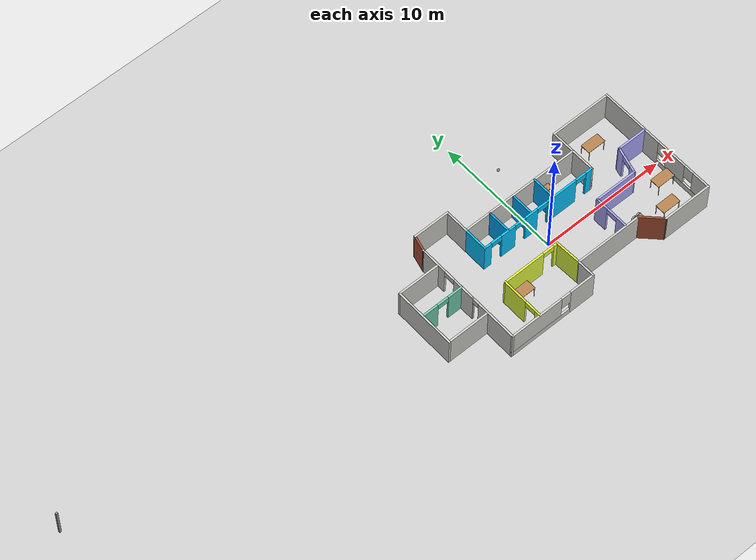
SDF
<sdf version="1.6">
 <world name="default">
  <plugin name="hello" filename="libwelcome_message.so"/>
  <light name="sun" type="directional">
   <pose>0 0 10 0 -0 0</pose>
   <diffuse>0.8 0.8 0.8 1</diffuse>
   <specular>0.2 0.2 0.2 1</specular>
   <attenuation>
    <range>1000</range>
    <constant>0.9</constant>
    <linear>0.01</linear>
    <quadratic>0.001</quadratic>
   </attenuation>
   <direction>-0.5 0.1 -0.9</direction>
  </light>
  <model name="ground_plane">
   <static>1</static>
   <link name="link">
    <collision name="collision">
     <geometry><plane><normal>0 0 1</normal><size>100 100</size></plane></geometry>
     <surface><friction><ode><mu>100</mu><mu2>50</mu2></ode></friction></surface>
    </collision>
    <visual name="visual">
     <cast_shadows>0</cast_shadows>
     <geometry><plane><normal>0 0 1</normal><size>100 100</size></plane></geometry>
     <material>
      <script><uri>file://media/materials/scripts/gazebo.material</uri><name>Gazebo/Grey</name></script>
     </material>
    </visual>
   </link>
  </model>
  <gravity>0 0 -9.8</gravity>
  <magnetic_field>6e-06 2.3e-05 -4.2e-05</magnetic_field>
  <atmosphere type="adiabatic"/>
  <physics name="default_physics" default="0" type="ode">
   <max_step_size>0.001</max_step_size>
   <real_time_factor>1</real_time_factor>
   <real_time_update_rate>1000</real_time_update_rate>
  </physics>
  <scene><ambient>0.4 0.4 0.4 1</ambient><background>0.7 0.7 0.7 1</background><shadows>1</shadows></scene>
  <spherical_coordinates>
   <surface_model>EARTH_WGS84</surface_model>
   <latitude_deg>0</latitude_deg>
   <longitude_deg>0</longitude_deg>
   <elevation>0</elevation>
   <heading_deg>0</heading_deg>
  </spherical_coordinates>
  <model name="Building">
   <pose>-13.8443 0.24841 0 0 -0 0</pose>
   <link name="Wall_10">
    <collision name="Wall_10_Collision">
     <geometry><box><size>4 0.15 2.5</size></box></geometry>
     <pose>0 0 1.25 0 -0 0</pose>
    </collision>
    <visual name="Wall_10_Visual">
     <pose>0 0 1.25 0 -0 0</pose>
     <geometry><box><size>4 0.15 2.5</size></box></geometry>
     <material>
      <script><uri>file://media/materials/scripts/gazebo.material</uri><name>Gazebo/CeilingTiled</name></script>
      <ambient>1 1 1 1</ambient>
     </material>
     <meta><layer>0</layer></meta>
    </visual>
    <pose>21.9406 -4.91227 0 0 -0 3.14159</pose>
   </link>
   <link name="Wall_11">
    <collision name="Wall_11_Collision">
     <geometry><box><size>2 0.15 2.5</size></box></geometry>
     <pose>0 0 1.25 0 -0 0</pose>
    </collision>
    <visual name="Wall_11_Visual">
     <pose>0 0 1.25 0 -0 0</pose>
     <geometry><box><size>2 0.15 2.5</size></box></geometry>
     <material>
      <script><uri>file://media/materials/scripts/gazebo.material</uri><name>Gazebo/Bricks</name></script>
      <ambient>1 1 1 1</ambient>
     </material>
     <meta><layer>0</layer></meta>
    </visual>
    <pose>19.3615 -4.25819 0 0 -0 2.35619</pose>
   </link>
   <link name="Wall_12">
    <collision name="Wall_12_Collision">
     <geometry><box><size>5.5 0.15 2.5</size></box></geometry>
     <pose>0 0 1.25 0 -0 0</pose>
    </collision>
    <visual name="Wall_12_Visual">
     <pose>0 0 1.25 0 -0 0</pose>
     <geometry><box><size>5.5 0.15 2.5</size></box></geometry>
     <material>
      <script><uri>file://media/materials/scripts/gazebo.material</uri><name>Gazebo/CeilingTiled</name></script>
      <ambient>1 1 1 1</ambient>
     </material>
     <meta><layer>0</layer></meta>
    </visual>
    <pose>16.0324 -3.60412 0 0 -0 3.14159</pose>
   </link>
   <link name="Wall_13">
    <collision name="Wall_13_Collision">
     <geometry><box><size>1.5 0.15 2.5</size></box></geometry>
     <pose>0 0 1.25 0 -0 0</pose>
    </collision>
    <visual name="Wall_13_Visual">
     <pose>0 0 1.25 0 -0 0</pose>
     <geometry><box><size>1.5 0.15 2.5</size></box></geometry>
     <material>
      <script><uri>file://media/materials/scripts/gazebo.material</uri><name>Gazebo/CeilingTiled</name></script>
      <ambient>0.901961 1 0.254902 1</ambient>
     </material>
     <meta><layer>0</layer></meta>
    </visual>
    <pose>13.3574 -4.27912 0 0 0 -1.5708</pose>
   </link>
   <link name="Wall_14">
    <pose>9.80745 -4.95412 0 0 -0 3.14159</pose>
    <visual name="Wall_14_Visual_0">
     <pose>-2.58123 0 1.25 0 -0 0</pose>
     <geometry><box><size>2.08753 0.15 2.5</size></box></geometry>
     <material>
      <script><uri>file://media/materials/scripts/gazebo.material</uri><name>Gazebo/CeilingTiled</name></script>
      <ambient>1 1 1 1</ambient>
     </material>
     <meta><layer>0</layer></meta>
    </visual>
    <collision name="Wall_14_Collision_0">
     <geometry><box><size>2.08753 0.15 2.5</size></box></geometry>
     <pose>-2.58123 0 1.25 0 -0 0</pose>
    </collision>
    <visual name="Wall_14_Visual_1">
     <pose>1.04377 0 0.25 0 -0 0</pose>
     <geometry><box><size>5.16247 0.15 0.5</size></box></geometry>
     <material>
      <script><uri>file://media/materials/scripts/gazebo.material</uri><name>Gazebo/CeilingTiled</name></script>
      <ambient>1 1 1 1</ambient>
     </material>
     <meta><layer>0</layer></meta>
    </visual>
    <collision name="Wall_14_Collision_1">
     <geometry><box><size>5.16247 0.15 0.5</size></box></geometry>
     <pose>1.04377 0 0.25 0 -0 0</pose>
    </collision>
    <visual name="Wall_14_Visual_2">
     <pose>1.44377 0 1.5 0 -0 0</pose>
     <geometry><box><size>4.36247 0.15 2</size></box></geometry>
     <material>
      <script><uri>file://media/materials/scripts/gazebo.material</uri><name>Gazebo/CeilingTiled</name></script>
      <ambient>1 1 1 1</ambient>
     </material>
     <meta><layer>0</layer></meta>
    </visual>
    <collision name="Wall_14_Collision_2">
     <geometry><box><size>4.36247 0.15 2</size></box></geometry>
     <pose>1.44377 0 1.5 0 -0 0</pose>
    </collision>
    <visual name="Wall_14_Visual_3">
     <pose>-1.13747 0 1.9 0 -0 0</pose>
     <geometry><box><size>0.8 0.15 1.2</size></box></geometry>
     <material>
      <script><uri>file://media/materials/scripts/gazebo.material</uri><name>Gazebo/CeilingTiled</name></script>
      <ambient>1 1 1 1</ambient>
     </material>
     <meta><layer>0</layer></meta>
    </visual>
    <collision name="Wall_14_Collision_3">
     <geometry><box><size>0.8 0.15 1.2</size></box></geometry>
     <pose>-1.13747 0 1.9 0 -0 0</pose>
    </collision>
   </link>
   <link name="Wall_15">
    <pose>6.25745 -3.02912 0 0 -0 1.5708</pose>
    <visual name="Wall_15_Visual_0">
     <pose>-0.337699 0 1.25 0 -0 0</pose>
     <geometry><box><size>3.3246 0.15 2.5</size></box></geometry>
     <material>
      <script><uri>file://media/materials/scripts/gazebo.material</uri><name>Gazebo/CeilingTiled</name></script>
      <ambient>0.435294 0.796078 0.67451 1</ambient>
     </material>
     <meta><layer>0</layer></meta>
    </visual>
    <collision name="Wall_15_Collision_0">
     <geometry><box><size>3.3246 0.15 2.5</size></box></geometry>
     <pose>-0.337699 0 1.25 0 -0 0</pose>
    </collision>
    <visual name="Wall_15_Visual_1">
     <pose>1.6623 0 2.25 0 -0 0</pose>
     <geometry><box><size>0.675399 0.15 0.5</size></box></geometry>
     <material>
      <script><uri>file://media/materials/scripts/gazebo.material</uri><name>Gazebo/CeilingTiled</name></script>
      <ambient>0.435294 0.796078 0.67451 1</ambient>
     </material>
     <meta><layer>0</layer></meta>
    </visual>
    <collision name="Wall_15_Collision_1">
     <geometry><box><size>0.675399 0.15 0.5</size></box></geometry>
     <pose>1.6623 0 2.25 0 -0 0</pose>
    </collision>
   </link>
   <link name="Wall_19">
    <collision name="Wall_19_Collision">
     <geometry><box><size>0.15 0.15 2.5</size></box></geometry>
     <pose>0 0 1.25 0 -0 0</pose>
    </collision>
    <visual name="Wall_19_Visual">
     <pose>0 0 1.25 0 -0 0</pose>
     <geometry><box><size>0.15 0.15 2.5</size></box></geometry>
     <material>
      <script><uri>file://media/materials/scripts/gazebo.material</uri><name>Gazebo/Grey</name></script>
      <ambient>1 1 1 1</ambient>
     </material>
     <meta><layer>0</layer></meta>
    </visual>
    <pose>6.25745 3.74588 0 0 -0 0</pose>
   </link>
   <link name="Wall_24">
    <collision name="Wall_24_Collision">
     <geometry><box><size>0.15 0.15 2.5</size></box></geometry>
     <pose>0 0 1.25 0 -0 0</pose>
    </collision>
    <visual name="Wall_24_Visual">
     <pose>0 0 1.25 0 -0 0</pose>
     <geometry><box><size>0.15 0.15 2.5</size></box></geometry>
     <material>
      <script><uri>file://media/materials/scripts/gazebo.material</uri><name>Gazebo/Grey</name></script>
      <ambient>1 1 1 1</ambient>
     </material>
     <meta><layer>0</layer></meta>
    </visual>
    <pose>-23.8656 4.2525 0 0 -0 0</pose>
   </link>
   <link name="Wall_26">
    <collision name="Wall_26_Collision">
     <geometry><box><size>3 0.15 2.5</size></box></geometry>
     <pose>0 0 1.25 0 -0 0</pose>
    </collision>
    <visual name="Wall_26_Visual">
     <pose>0 0 1.25 0 -0 0</pose>
     <geometry><box><size>3 0.15 2.5</size></box></geometry>
     <material>
      <script><uri>file://media/materials/scripts/gazebo.material</uri><name>Gazebo/CeilingTiled</name></script>
      <ambient>0.435294 0.796078 0.67451 1</ambient>
     </material>
     <meta><layer>0</layer></meta>
    </visual>
    <pose>7.99059 4.93773 0 0 -0 3.14159</pose>
   </link>
   <link name="Wall_27">
    <collision name="Wall_27_Collision">
     <geometry><box><size>1.38104 0.15 2.5</size></box></geometry>
     <pose>0 0 1.25 0 -0 0</pose>
    </collision>
    <visual name="Wall_27_Visual">
     <pose>0 0 1.25 0 -0 0</pose>
     <geometry><box><size>1.38104 0.15 2.5</size></box></geometry>
     <material>
      <script><uri>file://media/materials/scripts/gazebo.material</uri><name>Gazebo/Bricks</name></script>
      <ambient>0.435294 0.796078 0.67451 1</ambient>
     </material>
     <meta><layer>0</layer></meta>
    </visual>
    <pose>6.41152 4.34181 0 0 0 -1.8238</pose>
   </link>
   <link name="Wall_28">
    <collision name="Wall_28_Collision">
     <geometry><box><size>0.16 0.15 2.5</size></box></geometry>
     <pose>0 0 1.25 0 -0 0</pose>
    </collision>
    <visual name="Wall_28_Visual">
     <pose>0 0 1.25 0 -0 0</pose>
     <geometry><box><size>0.16 0.15 2.5</size></box></geometry>
     <material>
      <script><uri>file://media/materials/scripts/gazebo.material</uri><name>Gazebo/Grey</name></script>
      <ambient>1 1 1 1</ambient>
     </material>
     <meta><layer>0</layer></meta>
    </visual>
    <pose>6.26245 3.74588 0 0 -0 0</pose>
   </link>
   <link name="Wall_3">
    <collision name="Wall_3_Collision">
     <geometry><box><size>2.00019 0.15 2.5</size></box></geometry>
     <pose>0 0 1.25 0 -0 0</pose>
    </collision>
    <visual name="Wall_3_Visual">
     <pose>0 0 1.25 0 -0 0</pose>
     <geometry><box><size>2.00019 0.15 2.5</size></box></geometry>
     <material>
      <script><uri>file://media/materials/scripts/gazebo.material</uri><name>Gazebo/CeilingTiled</name></script>
      <ambient>1 1 1 1</ambient>
     </material>
     <meta><layer>0</layer></meta>
    </visual>
    <pose>9.41559 4.01273 0 0 0 -1.5708</pose>
   </link>
   <link name="Wall_30">
    <pose>6.25745 1.32088 0 0 0 -1.5708</pose>
    <visual name="Wall_30_Visual_0">
     <pose>-1.39411 0 1.25 0 -0 0</pose>
     <geometry><box><size>2.21177 0.15 2.5</size></box></geometry>
     <material>
      <script><uri>file://media/materials/scripts/gazebo.material</uri><name>Gazebo/CeilingTiled</name></script>
      <ambient>0.435294 0.796078 0.67451 1</ambient>
     </material>
     <meta><layer>0</layer></meta>
    </visual>
    <collision name="Wall_30_Collision_0">
     <geometry><box><size>2.21177 0.15 2.5</size></box></geometry>
     <pose>-1.39411 0 1.25 0 -0 0</pose>
    </collision>
    <visual name="Wall_30_Visual_1">
     <pose>1.55588 0 1.25 0 -0 0</pose>
     <geometry><box><size>1.88823 0.15 2.5</size></box></geometry>
     <material>
      <script><uri>file://media/materials/scripts/gazebo.material</uri><name>Gazebo/CeilingTiled</name></script>
      <ambient>0.435294 0.796078 0.67451 1</ambient>
     </material>
     <meta><layer>0</layer></meta>
    </visual>
    <collision name="Wall_30_Collision_1">
     <geometry><box><size>1.88823 0.15 2.5</size></box></geometry>
     <pose>1.55588 0 1.25 0 -0 0</pose>
    </collision>
    <visual name="Wall_30_Visual_2">
     <pose>0.16177 0 2.25 0 -0 0</pose>
     <geometry><box><size>0.9 0.15 0.5</size></box></geometry>
     <material>
      <script><uri>file://media/materials/scripts/gazebo.material</uri><name>Gazebo/CeilingTiled</name></script>
      <ambient>0.435294 0.796078 0.67451 1</ambient>
     </material>
     <meta><layer>0</layer></meta>
    </visual>
    <collision name="Wall_30_Collision_2">
     <geometry><box><size>0.9 0.15 0.5</size></box></geometry>
     <pose>0.16177 0 2.25 0 -0 0</pose>
    </collision>
   </link>
   <link name="Wall_31">
    <collision name="Wall_31_Collision">
     <geometry><box><size>0.15 0.15 2.5</size></box></geometry>
     <pose>0 0 1.25 0 -0 0</pose>
    </collision>
    <visual name="Wall_31_Visual">
     <pose>0 0 1.25 0 -0 0</pose>
     <geometry><box><size>0.15 0.15 2.5</size></box></geometry>
     <material>
      <script><uri>file://media/materials/scripts/gazebo.material</uri><name>Gazebo/Grey</name></script>
      <ambient>1 1 1 1</ambient>
     </material>
     <meta><layer>0</layer></meta>
    </visual>
    <pose>6.25745 -1.10412 0 0 -0 0</pose>
   </link>
   <link name="Wall_4">
    <collision name="Wall_4_Collision">
     <geometry><box><size>9.75 0.15 2.5</size></box></geometry>
     <pose>0 0 1.25 0 -0 0</pose>
    </collision>
    <visual name="Wall_4_Visual">
     <pose>0 0 1.25 0 -0 0</pose>
     <geometry><box><size>9.75 0.15 2.5</size></box></geometry>
     <material>
      <script><uri>file://media/materials/scripts/gazebo.material</uri><name>Gazebo/CeilingTiled</name></script>
      <ambient>0.0196078 0.690196 1 1</ambient>
     </material>
     <meta><layer>0</layer></meta>
    </visual>
    <pose>14.2156 3.08773 0 0 -0 0</pose>
   </link>
   <link name="Wall_40">
    <collision name="Wall_40_Collision">
     <geometry><box><size>3.5 0.15 2.5</size></box></geometry>
     <pose>0 0 1.25 0 -0 0</pose>
    </collision>
    <visual name="Wall_40_Visual">
     <pose>0 0 1.25 0 -0 0</pose>
     <geometry><box><size>3.5 0.15 2.5</size></box></geometry>
     <material>
      <script><uri>file://media/materials/scripts/gazebo.material</uri><name>Gazebo/CeilingTiled</name></script>
      <ambient>0.435294 0.796078 0.67451 1</ambient>
     </material>
     <meta><layer>0</layer></meta>
    </visual>
    <pose>4.56509 2.27847 0 0 -0 3.14159</pose>
   </link>
   <link name="Wall_41">
    <collision name="Wall_41_Collision">
     <geometry><box><size>5 0.15 2.5</size></box></geometry>
     <pose>0 0 1.25 0 -0 0</pose>
    </collision>
    <visual name="Wall_41_Visual">
     <pose>0 0 1.25 0 -0 0</pose>
     <geometry><box><size>5 0.15 2.5</size></box></geometry>
     <material>
      <script><uri>file://media/materials/scripts/gazebo.material</uri><name>Gazebo/CeilingTiled</name></script>
      <ambient>1 1 1 1</ambient>
     </material>
     <meta><layer>0</layer></meta>
    </visual>
    <pose>2.89009 -0.146525 0 0 0 -1.5708</pose>
   </link>
   <link name="Wall_42">
    <collision name="Wall_42_Collision">
     <geometry><box><size>3.5 0.15 2.5</size></box></geometry>
     <pose>0 0 1.25 0 -0 0</pose>
    </collision>
    <visual name="Wall_42_Visual">
     <pose>0 0 1.25 0 -0 0</pose>
     <geometry><box><size>3.5 0.15 2.5</size></box></geometry>
     <material>
      <script><uri>file://media/materials/scripts/gazebo.material</uri><name>Gazebo/CeilingTiled</name></script>
      <ambient>0.435294 0.796078 0.67451 1</ambient>
     </material>
     <meta><layer>0</layer></meta>
    </visual>
    <pose>4.56509 -2.57152 0 0 -0 0</pose>
   </link>
   <link name="Wall_44">
    <pose>4.59198 0.004767 0 0 -0 0</pose>
    <visual name="Wall_44_Visual_0">
     <pose>-1.08923 0 1.25 0 -0 0</pose>
     <geometry><box><size>1.32154 0.15 2.5</size></box></geometry>
     <material>
      <script><uri>file://media/materials/scripts/gazebo.material</uri><name>Gazebo/Grey</name></script>
      <ambient>0.435294 0.796078 0.67451 1</ambient>
     </material>
     <meta><layer>0</layer></meta>
    </visual>
    <collision name="Wall_44_Collision_0">
     <geometry><box><size>1.32154 0.15 2.5</size></box></geometry>
     <pose>-1.08923 0 1.25 0 -0 0</pose>
    </collision>
    <visual name="Wall_44_Visual_1">
     <pose>1.11077 0 1.25 0 -0 0</pose>
     <geometry><box><size>1.27846 0.15 2.5</size></box></geometry>
     <material>
      <script><uri>file://media/materials/scripts/gazebo.material</uri><name>Gazebo/Grey</name></script>
      <ambient>0.435294 0.796078 0.67451 1</ambient>
     </material>
     <meta><layer>0</layer></meta>
    </visual>
    <collision name="Wall_44_Collision_1">
     <geometry><box><size>1.27846 0.15 2.5</size></box></geometry>
     <pose>1.11077 0 1.25 0 -0 0</pose>
    </collision>
    <visual name="Wall_44_Visual_2">
     <pose>0.021536 0 2.25 0 -0 0</pose>
     <geometry><box><size>0.9 0.15 0.5</size></box></geometry>
     <material>
      <script><uri>file://media/materials/scripts/gazebo.material</uri><name>Gazebo/Grey</name></script>
      <ambient>0.435294 0.796078 0.67451 1</ambient>
     </material>
     <meta><layer>0</layer></meta>
    </visual>
    <collision name="Wall_44_Collision_2">
     <geometry><box><size>0.9 0.15 0.5</size></box></geometry>
     <pose>0.021536 0 2.25 0 -0 0</pose>
    </collision>
   </link>
   <link name="Wall_46">
    <collision name="Wall_46_Collision">
     <geometry><box><size>2 0.15 2.5</size></box></geometry>
     <pose>0 0 1.25 0 -0 0</pose>
    </collision>
    <visual name="Wall_46_Visual">
     <pose>0 0 1.25 0 -0 0</pose>
     <geometry><box><size>2 0.15 2.5</size></box></geometry>
     <material>
      <script><uri>file://media/materials/scripts/gazebo.material</uri><name>Gazebo/Grey</name></script>
      <ambient>0.0313726 0.776471 1 1</ambient>
     </material>
     <meta><layer>0</layer></meta>
    </visual>
    <pose>9.41559 2.16273 0 0 0 -1.5708</pose>
   </link>
   <link name="Wall_47">
    <pose>14.2156 1.23773 0 0 -0 0</pose>
    <visual name="Wall_47_Visual_0">
     <pose>-4.56019 0 1.25 0 -0 0</pose>
     <geometry><box><size>0.629619 0.15 2.5</size></box></geometry>
     <material>
      <script><uri>file://media/materials/scripts/gazebo.material</uri><name>Gazebo/Grey</name></script>
      <ambient>0.0313726 0.776471 1 1</ambient>
     </material>
     <meta><layer>0</layer></meta>
    </visual>
    <collision name="Wall_47_Collision_0">
     <geometry><box><size>0.629619 0.15 2.5</size></box></geometry>
     <pose>-4.56019 0 1.25 0 -0 0</pose>
    </collision>
    <visual name="Wall_47_Visual_1">
     <pose>-2.72849 0 1.25 0 -0 0</pose>
     <geometry><box><size>1.23379 0.15 2.5</size></box></geometry>
     <material>
      <script><uri>file://media/materials/scripts/gazebo.material</uri><name>Gazebo/Grey</name></script>
      <ambient>0.0313726 0.776471 1 1</ambient>
     </material>
     <meta><layer>0</layer></meta>
    </visual>
    <collision name="Wall_47_Collision_1">
     <geometry><box><size>1.23379 0.15 2.5</size></box></geometry>
     <pose>-2.72849 0 1.25 0 -0 0</pose>
    </collision>
    <visual name="Wall_47_Visual_2">
     <pose>-0.673405 0 1.25 0 -0 0</pose>
     <geometry><box><size>1.07638 0.15 2.5</size></box></geometry>
     <material>
      <script><uri>file://media/materials/scripts/gazebo.material</uri><name>Gazebo/Grey</name></script>
      <ambient>0.0313726 0.776471 1 1</ambient>
     </material>
     <meta><layer>0</layer></meta>
    </visual>
    <collision name="Wall_47_Collision_2">
     <geometry><box><size>1.07638 0.15 2.5</size></box></geometry>
     <pose>-0.673405 0 1.25 0 -0 0</pose>
    </collision>
    <visual name="Wall_47_Visual_3">
     <pose>2.0463 0 1.25 0 -0 0</pose>
     <geometry><box><size>2.56303 0.15 2.5</size></box></geometry>
     <material>
      <script><uri>file://media/materials/scripts/gazebo.material</uri><name>Gazebo/Grey</name></script>
      <ambient>0.0313726 0.776471 1 1</ambient>
     </material>
     <meta><layer>0</layer></meta>
    </visual>
    <collision name="Wall_47_Collision_3">
     <geometry><box><size>2.56303 0.15 2.5</size></box></geometry>
     <pose>2.0463 0 1.25 0 -0 0</pose>
    </collision>
    <visual name="Wall_47_Visual_4">
     <pose>4.55141 0 1.25 0 -0 0</pose>
     <geometry><box><size>0.647184 0.15 2.5</size></box></geometry>
     <material>
      <script><uri>file://media/materials/scripts/gazebo.material</uri><name>Gazebo/Grey</name></script>
      <ambient>0.0313726 0.776471 1 1</ambient>
     </material>
     <meta><layer>0</layer></meta>
    </visual>
    <collision name="Wall_47_Collision_4">
     <geometry><box><size>0.647184 0.15 2.5</size></box></geometry>
     <pose>4.55141 0 1.25 0 -0 0</pose>
    </collision>
    <visual name="Wall_47_Visual_5">
     <pose>-3.79538 0 2.25 0 -0 0</pose>
     <geometry><box><size>0.9 0.15 0.5</size></box></geometry>
     <material>
      <script><uri>file://media/materials/scripts/gazebo.material</uri><name>Gazebo/Grey</name></script>
      <ambient>0.0313726 0.776471 1 1</ambient>
     </material>
     <meta><layer>0</layer></meta>
    </visual>
    <collision name="Wall_47_Collision_5">
     <geometry><box><size>0.9 0.15 0.5</size></box></geometry>
     <pose>-3.79538 0 2.25 0 -0 0</pose>
    </collision>
    <visual name="Wall_47_Visual_6">
     <pose>-1.66159 0 2.25 0 -0 0</pose>
     <geometry><box><size>0.9 0.15 0.5</size></box></geometry>
     <material>
      <script><uri>file://media/materials/scripts/gazebo.material</uri><name>Gazebo/Grey</name></script>
      <ambient>0.0313726 0.776471 1 1</ambient>
     </material>
     <meta><layer>0</layer></meta>
    </visual>
    <collision name="Wall_47_Collision_6">
     <geometry><box><size>0.9 0.15 0.5</size></box></geometry>
     <pose>-1.66159 0 2.25 0 -0 0</pose>
    </collision>
    <visual name="Wall_47_Visual_7">
     <pose>0.314784 0 2.25 0 -0 0</pose>
     <geometry><box><size>0.9 0.15 0.5</size></box></geometry>
     <material>
      <script><uri>file://media/materials/scripts/gazebo.material</uri><name>Gazebo/Grey</name></script>
      <ambient>0.0313726 0.776471 1 1</ambient>
     </material>
     <meta><layer>0</layer></meta>
    </visual>
    <collision name="Wall_47_Collision_7">
     <geometry><box><size>0.9 0.15 0.5</size></box></geometry>
     <pose>0.314784 0 2.25 0 -0 0</pose>
    </collision>
    <visual name="Wall_47_Visual_8">
     <pose>3.77782 0 2.25 0 -0 0</pose>
     <geometry><box><size>0.9 0.15 0.5</size></box></geometry>
     <material>
      <script><uri>file://media/materials/scripts/gazebo.material</uri><name>Gazebo/Grey</name></script>
      <ambient>0.0313726 0.776471 1 1</ambient>
     </material>
     <meta><layer>0</layer></meta>
    </visual>
    <collision name="Wall_47_Collision_8">
     <geometry><box><size>0.9 0.15 0.5</size></box></geometry>
     <pose>3.77782 0 2.25 0 -0 0</pose>
    </collision>
   </link>
   <link name="Wall_48">
    <collision name="Wall_48_Collision">
     <geometry><box><size>2 0.15 2.5</size></box></geometry>
     <pose>0 0 1.25 0 -0 0</pose>
    </collision>
    <visual name="Wall_48_Visual">
     <pose>0 0 1.25 0 -0 0</pose>
     <geometry><box><size>2 0.15 2.5</size></box></geometry>
     <material>
      <script><uri>file://media/materials/scripts/gazebo.material</uri><name>Gazebo/CeilingTiled</name></script>
      <ambient>0.0470588 0.745098 1 1</ambient>
     </material>
     <meta><layer>0</layer></meta>
    </visual>
    <pose>19.0156 2.16273 0 0 -0 1.5708</pose>
   </link>
   <link name="Wall_52">
    <collision name="Wall_52_Collision">
     <geometry><box><size>1.8816 0.15 2.5</size></box></geometry>
     <pose>0 0 1.25 0 -0 0</pose>
    </collision>
    <visual name="Wall_52_Visual">
     <pose>0 0 1.25 0 -0 0</pose>
     <geometry><box><size>1.8816 0.15 2.5</size></box></geometry>
     <material>
      <script><uri>file://media/materials/scripts/gazebo.material</uri><name>Gazebo/Grey</name></script>
      <ambient>0 0.666667 1 1</ambient>
     </material>
     <meta><layer>0</layer></meta>
    </visual>
    <pose>11.5046 2.1473 0 0 -0 1.5708</pose>
   </link>
   <link name="Wall_53">
    <collision name="Wall_53_Collision">
     <geometry><box><size>0.15 0.15 2.5</size></box></geometry>
     <pose>0 0 1.25 0 -0 0</pose>
    </collision>
    <visual name="Wall_53_Visual">
     <pose>0 0 1.25 0 -0 0</pose>
     <geometry><box><size>0.15 0.15 2.5</size></box></geometry>
     <material>
      <script><uri>file://media/materials/scripts/gazebo.material</uri><name>Gazebo/Grey</name></script>
      <ambient>1 1 1 1</ambient>
     </material>
     <meta><layer>0</layer></meta>
    </visual>
    <pose>11.5046 3.01306 0 0 -0 0</pose>
   </link>
   <link name="Wall_54">
    <collision name="Wall_54_Collision">
     <geometry><box><size>0.15 0.15 2.5</size></box></geometry>
     <pose>0 0 1.25 0 -0 0</pose>
    </collision>
    <visual name="Wall_54_Visual">
     <pose>0 0 1.25 0 -0 0</pose>
     <geometry><box><size>0.15 0.15 2.5</size></box></geometry>
     <material>
      <script><uri>file://media/materials/scripts/gazebo.material</uri><name>Gazebo/Grey</name></script>
      <ambient>1 1 1 1</ambient>
     </material>
     <meta><layer>0</layer></meta>
    </visual>
    <pose>11.5046 3.01306 0 0 -0 0</pose>
   </link>
   <link name="Wall_56">
    <collision name="Wall_56_Collision">
     <geometry><box><size>1.86438 0.15 2.5</size></box></geometry>
     <pose>0 0 1.25 0 -0 0</pose>
    </collision>
    <visual name="Wall_56_Visual">
     <pose>0 0 1.25 0 -0 0</pose>
     <geometry><box><size>1.86438 0.15 2.5</size></box></geometry>
     <material>
      <script><uri>file://media/materials/scripts/gazebo.material</uri><name>Gazebo/Grey</name></script>
      <ambient>0.0196078 0.690196 1 1</ambient>
     </material>
     <meta><layer>0</layer></meta>
    </visual>
    <pose>13.5859 2.19102 0 0 0 -1.5708</pose>
   </link>
   <link name="Wall_58">
    <collision name="Wall_58_Collision">
     <geometry><box><size>1.89936 0.15 2.5</size></box></geometry>
     <pose>0 0 1.25 0 -0 0</pose>
    </collision>
    <visual name="Wall_58_Visual">
     <pose>0 0 1.25 0 -0 0</pose>
     <geometry><box><size>1.89936 0.15 2.5</size></box></geometry>
     <material>
      <script><uri>file://media/materials/scripts/gazebo.material</uri><name>Gazebo/Grey</name></script>
      <ambient>0.0196078 0.690196 1 1</ambient>
     </material>
     <meta><layer>0</layer></meta>
    </visual>
    <pose>15.5273 2.19102 0 0 0 -1.5708</pose>
   </link>
   <link name="Wall_60">
    <collision name="Wall_60_Collision">
     <geometry><box><size>2.5 0.15 2.5</size></box></geometry>
     <pose>0 0 1.25 0 -0 0</pose>
    </collision>
    <visual name="Wall_60_Visual">
     <pose>0 0 1.25 0 -0 0</pose>
     <geometry><box><size>2.5 0.15 2.5</size></box></geometry>
     <material>
      <script><uri>file://media/materials/scripts/gazebo.material</uri><name>Gazebo/Grey</name></script>
      <ambient>0.666667 0.666667 1 1</ambient>
     </material>
     <meta><layer>0</layer></meta>
    </visual>
    <pose>22.6776 1.19409 0 0 -0 3.14159</pose>
   </link>
   <link name="Wall_61">
    <pose>21.2308 0.179869 0 0 0 -1.8326</pose>
    <visual name="Wall_61_Visual_0">
     <pose>-0.761229 0 1.25 0 -0 0</pose>
     <geometry><box><size>0.727543 0.15 2.5</size></box></geometry>
     <material>
      <script><uri>file://media/materials/scripts/gazebo.material</uri><name>Gazebo/Grey</name></script>
      <ambient>0.666667 0.666667 1 1</ambient>
     </material>
     <meta><layer>0</layer></meta>
    </visual>
    <collision name="Wall_61_Collision_0">
     <geometry><box><size>0.727543 0.15 2.5</size></box></geometry>
     <pose>-0.761229 0 1.25 0 -0 0</pose>
    </collision>
    <visual name="Wall_61_Visual_1">
     <pose>0.813771 0 1.25 0 -0 0</pose>
     <geometry><box><size>0.622457 0.15 2.5</size></box></geometry>
     <material>
      <script><uri>file://media/materials/scripts/gazebo.material</uri><name>Gazebo/Grey</name></script>
      <ambient>0.666667 0.666667 1 1</ambient>
     </material>
     <meta><layer>0</layer></meta>
    </visual>
    <collision name="Wall_61_Collision_1">
     <geometry><box><size>0.622457 0.15 2.5</size></box></geometry>
     <pose>0.813771 0 1.25 0 -0 0</pose>
    </collision>
    <visual name="Wall_61_Visual_2">
     <pose>0.052543 0 2.25 0 -0 0</pose>
     <geometry><box><size>0.9 0.15 0.5</size></box></geometry>
     <material>
      <script><uri>file://media/materials/scripts/gazebo.material</uri><name>Gazebo/Grey</name></script>
      <ambient>0.666667 0.666667 1 1</ambient>
     </material>
     <meta><layer>0</layer></meta>
    </visual>
    <collision name="Wall_61_Collision_2">
     <geometry><box><size>0.9 0.15 0.5</size></box></geometry>
     <pose>0.052543 0 2.25 0 -0 0</pose>
    </collision>
   </link>
   <link name="Wall_62">
    <collision name="Wall_62_Collision">
     <geometry><box><size>3.5 0.15 2.5</size></box></geometry>
     <pose>0 0 1.25 0 -0 0</pose>
    </collision>
    <visual name="Wall_62_Visual">
     <pose>0 0 1.25 0 -0 0</pose>
     <geometry><box><size>3.5 0.15 2.5</size></box></geometry>
     <material>
      <script><uri>file://media/materials/scripts/gazebo.material</uri><name>Gazebo/Grey</name></script>
      <ambient>0.666667 0.666667 1 1</ambient>
     </material>
     <meta><layer>0</layer></meta>
    </visual>
    <pose>19.2841 -0.834353 0 0 -0 3.14159</pose>
   </link>
   <link name="Wall_63">
    <pose>17.6088 -2.1638 0 0 0 -1.57096</pose>
    <visual name="Wall_63_Visual_0">
     <pose>-0.874701 0 1.25 0 -0 0</pose>
     <geometry><box><size>1.05971 0.15 2.5</size></box></geometry>
     <material>
      <script><uri>file://media/materials/scripts/gazebo.material</uri><name>Gazebo/Grey</name></script>
      <ambient>0.666667 0.666667 1 1</ambient>
     </material>
     <meta><layer>0</layer></meta>
    </visual>
    <collision name="Wall_63_Collision_0">
     <geometry><box><size>1.05971 0.15 2.5</size></box></geometry>
     <pose>-0.874701 0 1.25 0 -0 0</pose>
    </collision>
    <visual name="Wall_63_Visual_1">
     <pose>0.979857 0 1.25 0 -0 0</pose>
     <geometry><box><size>0.849402 0.15 2.5</size></box></geometry>
     <material>
      <script><uri>file://media/materials/scripts/gazebo.material</uri><name>Gazebo/Grey</name></script>
      <ambient>0.666667 0.666667 1 1</ambient>
     </material>
     <meta><layer>0</layer></meta>
    </visual>
    <collision name="Wall_63_Collision_1">
     <geometry><box><size>0.849402 0.15 2.5</size></box></geometry>
     <pose>0.979857 0 1.25 0 -0 0</pose>
    </collision>
    <visual name="Wall_63_Visual_2">
     <pose>0.105156 0 2.25 0 -0 0</pose>
     <geometry><box><size>0.9 0.15 0.5</size></box></geometry>
     <material>
      <script><uri>file://media/materials/scripts/gazebo.material</uri><name>Gazebo/Grey</name></script>
      <ambient>0.666667 0.666667 1 1</ambient>
     </material>
     <meta><layer>0</layer></meta>
    </visual>
    <collision name="Wall_63_Collision_2">
     <geometry><box><size>0.9 0.15 0.5</size></box></geometry>
     <pose>0.105156 0 2.25 0 -0 0</pose>
    </collision>
   </link>
   <link name="Wall_65">
    <pose>8.67121 -3.26992 0 0 -0 1.5708</pose>
    <visual name="Wall_65_Visual_0">
     <pose>-1.4915 0 1.25 0 -0 0</pose>
     <geometry><box><size>0.516993 0.15 2.5</size></box></geometry>
     <material>
      <script><uri>file://media/materials/scripts/gazebo.material</uri><name>Gazebo/Grey</name></script>
      <ambient>0.901961 1 0.254902 1</ambient>
     </material>
     <meta><layer>0</layer></meta>
    </visual>
    <collision name="Wall_65_Collision_0">
     <geometry><box><size>0.516993 0.15 2.5</size></box></geometry>
     <pose>-1.4915 0 1.25 0 -0 0</pose>
    </collision>
    <visual name="Wall_65_Visual_1">
     <pose>0.708497 0 1.25 0 -0 0</pose>
     <geometry><box><size>2.08301 0.15 2.5</size></box></geometry>
     <material>
      <script><uri>file://media/materials/scripts/gazebo.material</uri><name>Gazebo/Grey</name></script>
      <ambient>0.901961 1 0.254902 1</ambient>
     </material>
     <meta><layer>0</layer></meta>
    </visual>
    <collision name="Wall_65_Collision_1">
     <geometry><box><size>2.08301 0.15 2.5</size></box></geometry>
     <pose>0.708497 0 1.25 0 -0 0</pose>
    </collision>
    <visual name="Wall_65_Visual_2">
     <pose>-0.783007 0 2.25 0 -0 0</pose>
     <geometry><box><size>0.9 0.15 0.5</size></box></geometry>
     <material>
      <script><uri>file://media/materials/scripts/gazebo.material</uri><name>Gazebo/Grey</name></script>
      <ambient>0.901961 1 0.254902 1</ambient>
     </material>
     <meta><layer>0</layer></meta>
    </visual>
    <collision name="Wall_65_Collision_2">
     <geometry><box><size>0.9 0.15 0.5</size></box></geometry>
     <pose>-0.783007 0 2.25 0 -0 0</pose>
    </collision>
   </link>
   <link name="Wall_66">
    <pose>10.9712 -1.59492 0 0 -0 0</pose>
    <visual name="Wall_66_Visual_0">
     <pose>-0.664828 0 1.25 0 -0 0</pose>
     <geometry><box><size>3.42034 0.15 2.5</size></box></geometry>
     <material>
      <script><uri>file://media/materials/scripts/gazebo.material</uri><name>Gazebo/Grey</name></script>
      <ambient>0.901961 1 0.254902 1</ambient>
     </material>
     <meta><layer>0</layer></meta>
    </visual>
    <collision name="Wall_66_Collision_0">
     <geometry><box><size>3.42034 0.15 2.5</size></box></geometry>
     <pose>-0.664828 0 1.25 0 -0 0</pose>
    </collision>
    <visual name="Wall_66_Visual_1">
     <pose>2.16017 0 1.25 0 -0 0</pose>
     <geometry><box><size>0.429656 0.15 2.5</size></box></geometry>
     <material>
      <script><uri>file://media/materials/scripts/gazebo.material</uri><name>Gazebo/Grey</name></script>
      <ambient>0.901961 1 0.254902 1</ambient>
     </material>
     <meta><layer>0</layer></meta>
    </visual>
    <collision name="Wall_66_Collision_1">
     <geometry><box><size>0.429656 0.15 2.5</size></box></geometry>
     <pose>2.16017 0 1.25 0 -0 0</pose>
    </collision>
    <visual name="Wall_66_Visual_2">
     <pose>1.49534 0 2.25 0 -0 0</pose>
     <geometry><box><size>0.9 0.15 0.5</size></box></geometry>
     <material>
      <script><uri>file://media/materials/scripts/gazebo.material</uri><name>Gazebo/Grey</name></script>
      <ambient>0.901961 1 0.254902 1</ambient>
     </material>
     <meta><layer>0</layer></meta>
    </visual>
    <collision name="Wall_66_Collision_2">
     <geometry><box><size>0.9 0.15 0.5</size></box></geometry>
     <pose>1.49534 0 2.25 0 -0 0</pose>
    </collision>
   </link>
   <link name="Wall_67">
    <collision name="Wall_67_Collision">
     <geometry><box><size>2.16105 0.15 2.5</size></box></geometry>
     <pose>0 0 1.25 0 -0 0</pose>
    </collision>
    <visual name="Wall_67_Visual">
     <pose>0 0 1.25 0 -0 0</pose>
     <geometry><box><size>2.16105 0.15 2.5</size></box></geometry>
     <material>
      <script><uri>file://media/materials/scripts/gazebo.material</uri><name>Gazebo/Grey</name></script>
      <ambient>0.901961 1 0.254902 1</ambient>
     </material>
     <meta><layer>0</layer></meta>
    </visual>
    <pose>13.3143 -2.59952 0 0 0 -1.5279</pose>
   </link>
   <link name="Wall_7">
    <collision name="Wall_7_Collision">
     <geometry><box><size>2 0.15 2.5</size></box></geometry>
     <pose>0 0 1.25 0 -0 0</pose>
    </collision>
    <visual name="Wall_7_Visual">
     <pose>0 0 1.25 0 -0 0</pose>
     <geometry><box><size>2 0.15 2.5</size></box></geometry>
     <material>
      <script><uri>file://media/materials/scripts/gazebo.material</uri><name>Gazebo/CeilingTiled</name></script>
      <ambient>1 1 1 1</ambient>
     </material>
     <meta><layer>0</layer></meta>
    </visual>
    <pose>19.0156 4.01273 0 0 -0 1.5708</pose>
   </link>
   <link name="Wall_8">
    <collision name="Wall_8_Collision">
     <geometry><box><size>5 0.15 2.5</size></box></geometry>
     <pose>0 0 1.25 0 -0 0</pose>
    </collision>
    <visual name="Wall_8_Visual">
     <pose>0 0 1.25 0 -0 0</pose>
     <geometry><box><size>5 0.15 2.5</size></box></geometry>
     <material>
      <script><uri>file://media/materials/scripts/gazebo.material</uri><name>Gazebo/CeilingTiled</name></script>
      <ambient>1 1 1 1</ambient>
     </material>
     <meta><layer>0</layer></meta>
    </visual>
    <pose>21.4406 4.93773 0 0 -0 0</pose>
   </link>
   <link name="Wall_9">
    <pose>23.8656 0.012733 0 0 0 -1.5708</pose>
    <visual name="Wall_9_Visual_0">
     <pose>-2.39869 0 1.25 0 -0 0</pose>
     <geometry><box><size>5.20263 0.15 2.5</size></box></geometry>
     <material>
      <script><uri>file://media/materials/scripts/gazebo.material</uri><name>Gazebo/CeilingTiled</name></script>
      <ambient>1 1 1 1</ambient>
     </material>
     <meta><layer>0</layer></meta>
    </visual>
    <collision name="Wall_9_Collision_0">
     <geometry><box><size>5.20263 0.15 2.5</size></box></geometry>
     <pose>-2.39869 0 1.25 0 -0 0</pose>
    </collision>
    <visual name="Wall_9_Visual_1">
     <pose>2.60131 0 0.25 0 -0 0</pose>
     <geometry><box><size>4.79737 0.15 0.5</size></box></geometry>
     <material>
      <script><uri>file://media/materials/scripts/gazebo.material</uri><name>Gazebo/CeilingTiled</name></script>
      <ambient>1 1 1 1</ambient>
     </material>
     <meta><layer>0</layer></meta>
    </visual>
    <collision name="Wall_9_Collision_1">
     <geometry><box><size>4.79737 0.15 0.5</size></box></geometry>
     <pose>2.60131 0 0.25 0 -0 0</pose>
    </collision>
    <visual name="Wall_9_Visual_2">
     <pose>1.86191 0 1.5 0 -0 0</pose>
     <geometry><box><size>1.71857 0.15 2</size></box></geometry>
     <material>
      <script><uri>file://media/materials/scripts/gazebo.material</uri><name>Gazebo/CeilingTiled</name></script>
      <ambient>1 1 1 1</ambient>
     </material>
     <meta><layer>0</layer></meta>
    </visual>
    <collision name="Wall_9_Collision_2">
     <geometry><box><size>1.71857 0.15 2</size></box></geometry>
     <pose>1.86191 0 1.5 0 -0 0</pose>
    </collision>
    <visual name="Wall_9_Visual_3">
     <pose>4.2606 0 1.5 0 -0 0</pose>
     <geometry><box><size>1.4788 0.15 2</size></box></geometry>
     <material>
      <script><uri>file://media/materials/scripts/gazebo.material</uri><name>Gazebo/CeilingTiled</name></script>
      <ambient>1 1 1 1</ambient>
     </material>
     <meta><layer>0</layer></meta>
    </visual>
    <collision name="Wall_9_Collision_3">
     <geometry><box><size>1.4788 0.15 2</size></box></geometry>
     <pose>4.2606 0 1.5 0 -0 0</pose>
    </collision>
    <visual name="Wall_9_Visual_4">
     <pose>0.602629 0 1.9 0 -0 0</pose>
     <geometry><box><size>0.8 0.15 1.2</size></box></geometry>
     <material>
      <script><uri>file://media/materials/scripts/gazebo.material</uri><name>Gazebo/CeilingTiled</name></script>
      <ambient>1 1 1 1</ambient>
     </material>
     <meta><layer>0</layer></meta>
    </visual>
    <collision name="Wall_9_Collision_4">
     <geometry><box><size>0.8 0.15 1.2</size></box></geometry>
     <pose>0.602629 0 1.9 0 -0 0</pose>
    </collision>
    <visual name="Wall_9_Visual_5">
     <pose>3.1212 0 1.9 0 -0 0</pose>
     <geometry><box><size>0.8 0.15 1.2</size></box></geometry>
     <material>
      <script><uri>file://media/materials/scripts/gazebo.material</uri><name>Gazebo/CeilingTiled</name></script>
      <ambient>1 1 1 1</ambient>
     </material>
     <meta><layer>0</layer></meta>
    </visual>
    <collision name="Wall_9_Collision_5">
     <geometry><box><size>0.8 0.15 1.2</size></box></geometry>
     <pose>3.1212 0 1.9 0 -0 0</pose>
    </collision>
   </link>
   <static>1</static>
  </model>
  <model name="HumanoidRobot_0">
   <link name="link_15">
    <pose>0 0 -0.014438 0 -0 0</pose>
    <inertial>
     <mass>1</mass>
     <inertia>
      <ixx>0.166667</ixx>
      <ixy>0</ixy>
      <ixz>0</ixz>
      <iyy>0.166667</iyy>
      <iyz>0</iyz>
      <izz>0.166667</izz>
     </inertia>
    </inertial>
    <visual name="visual">
     <geometry><box><size>0.8 0.5 0.1</size></box></geometry>
     <material>
      <lighting>1</lighting>
      <script><uri>file://media/materials/scripts/gazebo.material</uri><name>Gazebo/Grey</name></script>
      <shader type="pixel"><normal_map>__default__</normal_map></shader>
      <ambient>0.3 0.3 0.3 1</ambient>
      <diffuse>0.7 0.7 0.7 1</diffuse>
      <specular>0.01 0.01 0.01 1</specular>
      <emissive>0 0 0 1</emissive>
     </material>
    </visual>
    <collision name="collision">
     <geometry><box><size>0.8 0.5 0.1</size></box></geometry>
     <surface>
      <friction>
       <ode><mu>1</mu><mu2>1</mu2><fdir1>0 0 0</fdir1><slip1>0</slip1><slip2>0</slip2></ode>
       <torsional>
        <coefficient>1</coefficient>
        <patch_radius>0</patch_radius>
        <surface_radius>0</surface_radius>
        <use_patch_radius>1</use_patch_radius>
        <ode><slip>0</slip></ode>
       </torsional>
      </friction>
      <bounce><restitution_coefficient>0</restitution_coefficient><threshold>1e+06</threshold></bounce>
      <contact>
       <collide_without_contact>0</collide_without_contact>
       <collide_without_contact_bitmask>1</collide_without_contact_bitmask>
       <collide_bitmask>1</collide_bitmask>
       <ode>
        <soft_cfm>0</soft_cfm>
        <soft_erp>0.2</soft_erp>
        <kp>1e+13</kp>
        <kd>1</kd>
        <max_vel>0.01</max_vel>
        <min_depth>0</min_depth>
       </ode>
       <bullet>
        <split_impulse>1</split_impulse>
        <split_impulse_penetration_threshold>-0.01</split_impulse_penetration_threshold>
        <soft_cfm>0</soft_cfm>
        <soft_erp>0.2</soft_erp>
        <kp>1e+13</kp>
        <kd>1</kd>
       </bullet>
      </contact>
     </surface>
    </collision>
   </link>
   <link name="link_17">
    <pose>0.2 -0.300019 -0.014438 1.5707 -0 0</pose>
    <inertial>
     <mass>1</mass>
     <inertia><ixx>0.145833</ixx><ixy>0</ixy><ixz>0</ixz><iyy>0.145833</iyy><iyz>0</iyz><izz>0.125</izz></inertia>
    </inertial>
    <visual name="visual">
     <geometry><cylinder><radius>0.2</radius><length>0.1</length></cylinder></geometry>
     <material>
      <lighting>1</lighting>
      <script><uri>file://media/materials/scripts/gazebo.material</uri><name>Gazebo/Grey</name></script>
      <shader type="pixel"><normal_map>__default__</normal_map></shader>
      <ambient>0.3 0.3 0.3 1</ambient>
      <diffuse>0.7 0.7 0.7 1</diffuse>
      <specular>0.01 0.01 0.01 1</specular>
      <emissive>0 0 0 1</emissive>
     </material>
    </visual>
    <collision name="collision">
     <geometry><cylinder><radius>0.2</radius><length>0.1</length></cylinder></geometry>
     <surface>
      <friction>
       <ode><mu>1</mu><mu2>1</mu2><fdir1>0 0 0</fdir1><slip1>0</slip1><slip2>0</slip2></ode>
       <torsional>
        <coefficient>1</coefficient>
        <patch_radius>0</patch_radius>
        <surface_radius>0</surface_radius>
        <use_patch_radius>1</use_patch_radius>
        <ode><slip>0</slip></ode>
       </torsional>
      </friction>
      <bounce><restitution_coefficient>0</restitution_coefficient><threshold>1e+06</threshold></bounce>
      <contact>
       <collide_without_contact>0</collide_without_contact>
       <collide_without_contact_bitmask>1</collide_without_contact_bitmask>
       <collide_bitmask>1</collide_bitmask>
       <ode>
        <soft_cfm>0</soft_cfm>
        <soft_erp>0.2</soft_erp>
        <kp>1e+13</kp>
        <kd>1</kd>
        <max_vel>0.01</max_vel>
        <min_depth>0</min_depth>
       </ode>
       <bullet>
        <split_impulse>1</split_impulse>
        <split_impulse_penetration_threshold>-0.01</split_impulse_penetration_threshold>
        <soft_cfm>0</soft_cfm>
        <soft_erp>0.2</soft_erp>
        <kp>1e+13</kp>
        <kd>1</kd>
       </bullet>
      </contact>
     </surface>
    </collision>
   </link>
   <link name="link_17_clone">
    <pose>0.2 0.300019 -0.014438 1.5707 -0 0</pose>
    <inertial>
     <mass>1</mass>
     <inertia><ixx>0.145833</ixx><ixy>0</ixy><ixz>0</ixz><iyy>0.145833</iyy><iyz>0</iyz><izz>0.125</izz></inertia>
    </inertial>
    <visual name="visual">
     <geometry><cylinder><radius>0.2</radius><length>0.1</length></cylinder></geometry>
     <material>
      <lighting>1</lighting>
      <script><uri>file://media/materials/scripts/gazebo.material</uri><name>Gazebo/Grey</name></script>
      <shader type="pixel"><normal_map>__default__</normal_map></shader>
      <ambient>0.3 0.3 0.3 1</ambient>
      <diffuse>0.7 0.7 0.7 1</diffuse>
      <specular>0.01 0.01 0.01 1</specular>
      <emissive>0 0 0 1</emissive>
     </material>
    </visual>
    <collision name="collision">
     <geometry><cylinder><radius>0.2</radius><length>0.1</length></cylinder></geometry>
     <surface>
      <friction>
       <ode><mu>1</mu><mu2>1</mu2><fdir1>0 0 0</fdir1><slip1>0</slip1><slip2>0</slip2></ode>
       <torsional>
        <coefficient>1</coefficient>
        <patch_radius>0</patch_radius>
        <surface_radius>0</surface_radius>
        <use_patch_radius>1</use_patch_radius>
        <ode><slip>0</slip></ode>
       </torsional>
      </friction>
      <bounce><restitution_coefficient>0</restitution_coefficient><threshold>1e+06</threshold></bounce>
      <contact>
       <collide_without_contact>0</collide_without_contact>
       <collide_without_contact_bitmask>1</collide_without_contact_bitmask>
       <collide_bitmask>1</collide_bitmask>
       <ode>
        <soft_cfm>0</soft_cfm>
        <soft_erp>0.2</soft_erp>
        <kp>1e+13</kp>
        <kd>1</kd>
        <max_vel>0.01</max_vel>
        <min_depth>0</min_depth>
       </ode>
       <bullet>
        <split_impulse>1</split_impulse>
        <split_impulse_penetration_threshold>-0.01</split_impulse_penetration_threshold>
        <soft_cfm>0</soft_cfm>
        <soft_erp>0.2</soft_erp>
        <kp>1e+13</kp>
        <kd>1</kd>
       </bullet>
      </contact>
     </surface>
    </collision>
   </link>
   <link name="link_17_clone_0">
    <pose>-0.2 -0.300019 -0.014438 1.5707 -0 0</pose>
    <inertial>
     <mass>1</mass>
     <inertia><ixx>0.145833</ixx><ixy>0</ixy><ixz>0</ixz><iyy>0.145833</iyy><iyz>0</iyz><izz>0.125</izz></inertia>
    </inertial>
    <visual name="visual">
     <geometry><cylinder><radius>0.2</radius><length>0.1</length></cylinder></geometry>
     <material>
      <lighting>1</lighting>
      <script><uri>file://media/materials/scripts/gazebo.material</uri><name>Gazebo/Grey</name></script>
      <shader type="pixel"><normal_map>__default__</normal_map></shader>
      <ambient>0.3 0.3 0.3 1</ambient>
      <diffuse>0.7 0.7 0.7 1</diffuse>
      <specular>0.01 0.01 0.01 1</specular>
      <emissive>0 0 0 1</emissive>
     </material>
    </visual>
    <collision name="collision">
     <geometry><cylinder><radius>0.2</radius><length>0.1</length></cylinder></geometry>
     <surface>
      <friction>
       <ode><mu>1</mu><mu2>1</mu2><fdir1>0 0 0</fdir1><slip1>0</slip1><slip2>0</slip2></ode>
       <torsional>
        <coefficient>1</coefficient>
        <patch_radius>0</patch_radius>
        <surface_radius>0</surface_radius>
        <use_patch_radius>1</use_patch_radius>
        <ode><slip>0</slip></ode>
       </torsional>
      </friction>
      <bounce><restitution_coefficient>0</restitution_coefficient><threshold>1e+06</threshold></bounce>
      <contact>
       <collide_without_contact>0</collide_without_contact>
       <collide_without_contact_bitmask>1</collide_without_contact_bitmask>
       <collide_bitmask>1</collide_bitmask>
       <ode>
        <soft_cfm>0</soft_cfm>
        <soft_erp>0.2</soft_erp>
        <kp>1e+13</kp>
        <kd>1</kd>
        <max_vel>0.01</max_vel>
        <min_depth>0</min_depth>
       </ode>
       <bullet>
        <split_impulse>1</split_impulse>
        <split_impulse_penetration_threshold>-0.01</split_impulse_penetration_threshold>
        <soft_cfm>0</soft_cfm>
        <soft_erp>0.2</soft_erp>
        <kp>1e+13</kp>
        <kd>1</kd>
       </bullet>
      </contact>
     </surface>
    </collision>
   </link>
   <link name="link_17_clone_1">
    <pose>-0.2 0.300019 -0.014438 1.5707 -0 0</pose>
    <inertial>
     <mass>1</mass>
     <inertia><ixx>0.145833</ixx><ixy>0</ixy><ixz>0</ixz><iyy>0.145833</iyy><iyz>0</iyz><izz>0.125</izz></inertia>
    </inertial>
    <visual name="visual">
     <geometry><cylinder><radius>0.2</radius><length>0.1</length></cylinder></geometry>
     <material>
      <lighting>1</lighting>
      <script><uri>file://media/materials/scripts/gazebo.material</uri><name>Gazebo/Grey</name></script>
      <shader type="pixel"><normal_map>__default__</normal_map></shader>
      <ambient>0.3 0.3 0.3 1</ambient>
      <diffuse>0.7 0.7 0.7 1</diffuse>
      <specular>0.01 0.01 0.01 1</specular>
      <emissive>0 0 0 1</emissive>
     </material>
    </visual>
    <collision name="collision">
     <geometry><cylinder><radius>0.2</radius><length>0.1</length></cylinder></geometry>
     <surface>
      <friction>
       <ode><mu>1</mu><mu2>1</mu2><fdir1>0 0 0</fdir1><slip1>0</slip1><slip2>0</slip2></ode>
       <torsional>
        <coefficient>1</coefficient>
        <patch_radius>0</patch_radius>
        <surface_radius>0</surface_radius>
        <use_patch_radius>1</use_patch_radius>
        <ode><slip>0</slip></ode>
       </torsional>
      </friction>
      <bounce><restitution_coefficient>0</restitution_coefficient><threshold>1e+06</threshold></bounce>
      <contact>
       <collide_without_contact>0</collide_without_contact>
       <collide_without_contact_bitmask>1</collide_without_contact_bitmask>
       <collide_bitmask>1</collide_bitmask>
       <ode>
        <soft_cfm>0</soft_cfm>
        <soft_erp>0.2</soft_erp>
        <kp>1e+13</kp>
        <kd>1</kd>
        <max_vel>0.01</max_vel>
        <min_depth>0</min_depth>
       </ode>
       <bullet>
        <split_impulse>1</split_impulse>
        <split_impulse_penetration_threshold>-0.01</split_impulse_penetration_threshold>
        <soft_cfm>0</soft_cfm>
        <soft_erp>0.2</soft_erp>
        <kp>1e+13</kp>
        <kd>1</kd>
       </bullet>
      </contact>
     </surface>
    </collision>
   </link>
   <link name="link_18">
    <pose>0 0 0.072192 0 -0 0</pose>
    <inertial>
     <mass>1</mass>
     <inertia><ixx>0.145833</ixx><ixy>0</ixy><ixz>0</ixz><iyy>0.145833</iyy><iyz>0</iyz><izz>0.125</izz></inertia>
    </inertial>
    <visual name="visual">
     <geometry><cylinder><radius>0.2</radius><length>0.2</length></cylinder></geometry>
     <material>
      <lighting>1</lighting>
      <script><uri>file://media/materials/scripts/gazebo.material</uri><name>Gazebo/Grey</name></script>
      <shader type="pixel"><normal_map>__default__</normal_map></shader>
      <ambient>0.3 0.3 0.3 1</ambient>
      <diffuse>0.7 0.7 0.7 1</diffuse>
      <specular>0.01 0.01 0.01 1</specular>
      <emissive>0 0 0 1</emissive>
     </material>
    </visual>
    <collision name="collision">
     <geometry><cylinder><radius>0.2</radius><length>0.2</length></cylinder></geometry>
     <surface>
      <friction>
       <ode><mu>1</mu><mu2>1</mu2><fdir1>0 0 0</fdir1><slip1>0</slip1><slip2>0</slip2></ode>
       <torsional>
        <coefficient>1</coefficient>
        <patch_radius>0</patch_radius>
        <surface_radius>0</surface_radius>
        <use_patch_radius>1</use_patch_radius>
        <ode><slip>0</slip></ode>
       </torsional>
      </friction>
      <bounce><restitution_coefficient>0</restitution_coefficient><threshold>1e+06</threshold></bounce>
      <contact>
       <collide_without_contact>0</collide_without_contact>
       <collide_without_contact_bitmask>1</collide_without_contact_bitmask>
       <collide_bitmask>1</collide_bitmask>
       <ode>
        <soft_cfm>0</soft_cfm>
        <soft_erp>0.2</soft_erp>
        <kp>1e+13</kp>
        <kd>1</kd>
        <max_vel>0.01</max_vel>
        <min_depth>0</min_depth>
       </ode>
       <bullet>
        <split_impulse>1</split_impulse>
        <split_impulse_penetration_threshold>-0.01</split_impulse_penetration_threshold>
        <soft_cfm>0</soft_cfm>
        <soft_erp>0.2</soft_erp>
        <kp>1e+13</kp>
        <kd>1</kd>
       </bullet>
      </contact>
     </surface>
    </collision>
   </link>
   <joint name="link_15_JOINT_1" type="revolute">
    <parent>link_15</parent>
    <child>link_17</child>
    <axis>
     <xyz>0 0 1</xyz>
     <use_parent_model_frame>0</use_parent_model_frame>
     <limit>
      <lower>-1.79769e+308</lower>
      <upper>1.79769e+308</upper>
      <effort>-1</effort>
      <velocity>-1</velocity>
     </limit>
     <dynamics>
      <spring_reference>0</spring_reference>
      <spring_stiffness>0</spring_stiffness>
      <damping>0</damping>
     </dynamics>
    </axis>
    <physics>
     <ode><limit><cfm>0</cfm><erp>0.2</erp></limit><suspension><cfm>0</cfm><erp>0.2</erp></suspension></ode>
    </physics>
   </joint>
   <joint name="link_15_JOINT_2" type="revolute">
    <parent>link_15</parent>
    <child>link_17_clone</child>
    <axis>
     <xyz>0 0 1</xyz>
     <use_parent_model_frame>0</use_parent_model_frame>
     <limit>
      <lower>-1.79769e+308</lower>
      <upper>1.79769e+308</upper>
      <effort>-1</effort>
      <velocity>-1</velocity>
     </limit>
     <dynamics>
      <spring_reference>0</spring_reference>
      <spring_stiffness>0</spring_stiffness>
      <damping>0</damping>
     </dynamics>
    </axis>
    <physics>
     <ode><limit><cfm>0</cfm><erp>0.2</erp></limit><suspension><cfm>0</cfm><erp>0.2</erp></suspension></ode>
    </physics>
   </joint>
   <joint name="link_15_JOINT_3" type="revolute">
    <parent>link_15</parent>
    <child>link_17_clone_0</child>
    <axis>
     <xyz>0 0 1</xyz>
     <use_parent_model_frame>0</use_parent_model_frame>
     <limit>
      <lower>-1.79769e+308</lower>
      <upper>1.79769e+308</upper>
      <effort>-1</effort>
      <velocity>-1</velocity>
     </limit>
     <dynamics>
      <spring_reference>0</spring_reference>
      <spring_stiffness>0</spring_stiffness>
      <damping>0</damping>
     </dynamics>
    </axis>
    <physics>
     <ode><limit><cfm>0</cfm><erp>0.2</erp></limit><suspension><cfm>0</cfm><erp>0.2</erp></suspension></ode>
    </physics>
   </joint>
   <joint name="link_15_JOINT_4" type="revolute">
    <parent>link_15</parent>
    <child>link_17_clone_1</child>
    <axis>
     <xyz>0 0 1</xyz>
     <use_parent_model_frame>0</use_parent_model_frame>
     <limit>
      <lower>-1.79769e+308</lower>
      <upper>1.79769e+308</upper>
      <effort>-1</effort>
      <velocity>-1</velocity>
     </limit>
     <dynamics>
      <spring_reference>0</spring_reference>
      <spring_stiffness>0</spring_stiffness>
      <damping>0</damping>
     </dynamics>
    </axis>
    <physics>
     <ode><limit><cfm>0</cfm><erp>0.2</erp></limit><suspension><cfm>0</cfm><erp>0.2</erp></suspension></ode>
    </physics>
   </joint>
   <joint name="link_15_JOINT_6" type="revolute">
    <parent>link_15</parent>
    <child>link_18</child>
    <axis>
     <xyz>0 0 1</xyz>
     <use_parent_model_frame>0</use_parent_model_frame>
     <limit>
      <lower>-1.79769e+308</lower>
      <upper>1.79769e+308</upper>
      <effort>-1</effort>
      <velocity>-1</velocity>
     </limit>
     <dynamics>
      <spring_reference>0</spring_reference>
      <spring_stiffness>0</spring_stiffness>
      <damping>0</damping>
     </dynamics>
    </axis>
    <physics>
     <ode><limit><cfm>0</cfm><erp>0.2</erp></limit><suspension><cfm>0</cfm><erp>0.2</erp></suspension></ode>
    </physics>
   </joint>
   <static>0</static>
   <pose>5.89182 -2.57077 0.214438 4e-06 -1.7e-05 0.022156</pose>
  </model>
  <model name="table">
   <static>1</static>
   <link name="link">
    <collision name="surface">
     <pose>0 0 1 0 -0 0</pose>
     <geometry><box><size>1.5 0.8 0.03</size></box></geometry>
     <surface><friction><ode><mu>0.6</mu><mu2>0.6</mu2></ode></friction></surface>
    </collision>
    <visual name="visual1">
     <pose>0 0 1 0 -0 0</pose>
     <geometry><box><size>1.5 0.8 0.03</size></box></geometry>
     <material>
      <script><uri>file://media/materials/scripts/gazebo.material</uri><name>Gazebo/Wood</name></script>
     </material>
    </visual>
    <collision name="front_left_leg">
     <pose>0.68 0.38 0.5 0 -0 0</pose>
     <geometry><cylinder><radius>0.02</radius><length>1</length></cylinder></geometry>
    </collision>
    <visual name="front_left_leg">
     <pose>0.68 0.38 0.5 0 -0 0</pose>
     <geometry><cylinder><radius>0.02</radius><length>1</length></cylinder></geometry>
     <material>
      <script><uri>file://media/materials/scripts/gazebo.material</uri><name>Gazebo/Grey</name></script>
     </material>
    </visual>
    <collision name="front_right_leg">
     <pose>0.68 -0.38 0.5 0 -0 0</pose>
     <geometry><cylinder><radius>0.02</radius><length>1</length></cylinder></geometry>
    </collision>
    <visual name="front_right_leg">
     <pose>0.68 -0.38 0.5 0 -0 0</pose>
     <geometry><cylinder><radius>0.02</radius><length>1</length></cylinder></geometry>
     <material>
      <script><uri>file://media/materials/scripts/gazebo.material</uri><name>Gazebo/Grey</name></script>
     </material>
    </visual>
    <collision name="back_right_leg">
     <pose>-0.68 -0.38 0.5 0 -0 0</pose>
     <geometry><cylinder><radius>0.02</radius><length>1</length></cylinder></geometry>
    </collision>
    <visual name="back_right_leg">
     <pose>-0.68 -0.38 0.5 0 -0 0</pose>
     <geometry><cylinder><radius>0.02</radius><length>1</length></cylinder></geometry>
     <material>
      <script><uri>file://media/materials/scripts/gazebo.material</uri><name>Gazebo/Grey</name></script>
     </material>
    </visual>
    <collision name="back_left_leg">
     <pose>-0.68 0.38 0.5 0 -0 0</pose>
     <geometry><cylinder><radius>0.02</radius><length>1</length></cylinder></geometry>
    </collision>
    <visual name="back_left_leg">
     <pose>-0.68 0.38 0.5 0 -0 0</pose>
     <geometry><cylinder><radius>0.02</radius><length>1</length></cylinder></geometry>
     <material>
      <script><uri>file://media/materials/scripts/gazebo.material</uri><name>Gazebo/Grey</name></script>
     </material>
    </visual>
   </link>
   <pose>7.82462 -3.25854 0 0 -0 0</pose>
  </model>
  <model name="table_0">
   <static>1</static>
   <link name="link">
    <collision name="surface">
     <pose>0 0 1 0 -0 0</pose>
     <geometry><box><size>1.5 0.8 0.03</size></box></geometry>
     <surface><friction><ode><mu>0.6</mu><mu2>0.6</mu2></ode></friction></surface>
    </collision>
    <visual name="visual1">
     <pose>0 0 1 0 -0 0</pose>
     <geometry><box><size>1.5 0.8 0.03</size></box></geometry>
     <material>
      <script><uri>file://media/materials/scripts/gazebo.material</uri><name>Gazebo/Wood</name></script>
     </material>
    </visual>
    <collision name="front_left_leg">
     <pose>0.68 0.38 0.5 0 -0 0</pose>
     <geometry><cylinder><radius>0.02</radius><length>1</length></cylinder></geometry>
    </collision>
    <visual name="front_left_leg">
     <pose>0.68 0.38 0.5 0 -0 0</pose>
     <geometry><cylinder><radius>0.02</radius><length>1</length></cylinder></geometry>
     <material>
      <script><uri>file://media/materials/scripts/gazebo.material</uri><name>Gazebo/Grey</name></script>
     </material>
    </visual>
    <collision name="front_right_leg">
     <pose>0.68 -0.38 0.5 0 -0 0</pose>
     <geometry><cylinder><radius>0.02</radius><length>1</length></cylinder></geometry>
    </collision>
    <visual name="front_right_leg">
     <pose>0.68 -0.38 0.5 0 -0 0</pose>
     <geometry><cylinder><radius>0.02</radius><length>1</length></cylinder></geometry>
     <material>
      <script><uri>file://media/materials/scripts/gazebo.material</uri><name>Gazebo/Grey</name></script>
     </material>
    </visual>
    <collision name="back_right_leg">
     <pose>-0.68 -0.38 0.5 0 -0 0</pose>
     <geometry><cylinder><radius>0.02</radius><length>1</length></cylinder></geometry>
    </collision>
    <visual name="back_right_leg">
     <pose>-0.68 -0.38 0.5 0 -0 0</pose>
     <geometry><cylinder><radius>0.02</radius><length>1</length></cylinder></geometry>
     <material>
      <script><uri>file://media/materials/scripts/gazebo.material</uri><name>Gazebo/Grey</name></script>
     </material>
    </visual>
    <collision name="back_left_leg">
     <pose>-0.68 0.38 0.5 0 -0 0</pose>
     <geometry><cylinder><radius>0.02</radius><length>1</length></cylinder></geometry>
    </collision>
    <visual name="back_left_leg">
     <pose>-0.68 0.38 0.5 0 -0 0</pose>
     <geometry><cylinder><radius>0.02</radius><length>1</length></cylinder></geometry>
     <material>
      <script><uri>file://media/materials/scripts/gazebo.material</uri><name>Gazebo/Grey</name></script>
     </material>
    </visual>
   </link>
   <pose>-4.09861 -1.93857 0 0 -0 0</pose>
  </model>
  <model name="table_1">
   <static>1</static>
   <link name="link">
    <collision name="surface">
     <pose>0 0 1 0 -0 0</pose>
     <geometry><box><size>1.5 0.8 0.03</size></box></geometry>
     <surface><friction><ode><mu>0.6</mu><mu2>0.6</mu2></ode></friction></surface>
    </collision>
    <visual name="visual1">
     <pose>0 0 1 0 -0 0</pose>
     <geometry><box><size>1.5 0.8 0.03</size></box></geometry>
     <material>
      <script><uri>file://media/materials/scripts/gazebo.material</uri><name>Gazebo/Wood</name></script>
     </material>
    </visual>
    <collision name="front_left_leg">
     <pose>0.68 0.38 0.5 0 -0 0</pose>
     <geometry><cylinder><radius>0.02</radius><length>1</length></cylinder></geometry>
    </collision>
    <visual name="front_left_leg">
     <pose>0.68 0.38 0.5 0 -0 0</pose>
     <geometry><cylinder><radius>0.02</radius><length>1</length></cylinder></geometry>
     <material>
      <script><uri>file://media/materials/scripts/gazebo.material</uri><name>Gazebo/Grey</name></script>
     </material>
    </visual>
    <collision name="front_right_leg">
     <pose>0.68 -0.38 0.5 0 -0 0</pose>
     <geometry><cylinder><radius>0.02</radius><length>1</length></cylinder></geometry>
    </collision>
    <visual name="front_right_leg">
     <pose>0.68 -0.38 0.5 0 -0 0</pose>
     <geometry><cylinder><radius>0.02</radius><length>1</length></cylinder></geometry>
     <material>
      <script><uri>file://media/materials/scripts/gazebo.material</uri><name>Gazebo/Grey</name></script>
     </material>
    </visual>
    <collision name="back_right_leg">
     <pose>-0.68 -0.38 0.5 0 -0 0</pose>
     <geometry><cylinder><radius>0.02</radius><length>1</length></cylinder></geometry>
    </collision>
    <visual name="back_right_leg">
     <pose>-0.68 -0.38 0.5 0 -0 0</pose>
     <geometry><cylinder><radius>0.02</radius><length>1</length></cylinder></geometry>
     <material>
      <script><uri>file://media/materials/scripts/gazebo.material</uri><name>Gazebo/Grey</name></script>
     </material>
    </visual>
    <collision name="back_left_leg">
     <pose>-0.68 0.38 0.5 0 -0 0</pose>
     <geometry><cylinder><radius>0.02</radius><length>1</length></cylinder></geometry>
    </collision>
    <visual name="back_left_leg">
     <pose>-0.68 0.38 0.5 0 -0 0</pose>
     <geometry><cylinder><radius>0.02</radius><length>1</length></cylinder></geometry>
     <material>
      <script><uri>file://media/materials/scripts/gazebo.material</uri><name>Gazebo/Grey</name></script>
     </material>
    </visual>
   </link>
   <pose>7.36272 3.5908 0 0 -0 0</pose>
  </model>
  <model name="table_clone">
   <static>1</static>
   <link name="link">
    <collision name="surface">
     <pose>0 0 1 0 -0 0</pose>
     <geometry><box><size>1.5 0.8 0.03</size></box></geometry>
     <surface><friction><ode><mu>0.6</mu><mu2>0.6</mu2></ode></friction></surface>
    </collision>
    <visual name="visual1">
     <pose>0 0 1 0 -0 0</pose>
     <geometry><box><size>1.5 0.8 0.03</size></box></geometry>
     <material>
      <script><uri>file://media/materials/scripts/gazebo.material</uri><name>Gazebo/Wood</name></script>
     </material>
    </visual>
    <collision name="front_left_leg">
     <pose>0.68 0.38 0.5 0 -0 0</pose>
     <geometry><cylinder><radius>0.02</radius><length>1</length></cylinder></geometry>
    </collision>
    <visual name="front_left_leg">
     <pose>0.68 0.38 0.5 0 -0 0</pose>
     <geometry><cylinder><radius>0.02</radius><length>1</length></cylinder></geometry>
     <material>
      <script><uri>file://media/materials/scripts/gazebo.material</uri><name>Gazebo/Grey</name></script>
     </material>
    </visual>
    <collision name="front_right_leg">
     <pose>0.68 -0.38 0.5 0 -0 0</pose>
     <geometry><cylinder><radius>0.02</radius><length>1</length></cylinder></geometry>
    </collision>
    <visual name="front_right_leg">
     <pose>0.68 -0.38 0.5 0 -0 0</pose>
     <geometry><cylinder><radius>0.02</radius><length>1</length></cylinder></geometry>
     <material>
      <script><uri>file://media/materials/scripts/gazebo.material</uri><name>Gazebo/Grey</name></script>
     </material>
    </visual>
    <collision name="back_right_leg">
     <pose>-0.68 -0.38 0.5 0 -0 0</pose>
     <geometry><cylinder><radius>0.02</radius><length>1</length></cylinder></geometry>
    </collision>
    <visual name="back_right_leg">
     <pose>-0.68 -0.38 0.5 0 -0 0</pose>
     <geometry><cylinder><radius>0.02</radius><length>1</length></cylinder></geometry>
     <material>
      <script><uri>file://media/materials/scripts/gazebo.material</uri><name>Gazebo/Grey</name></script>
     </material>
    </visual>
    <collision name="back_left_leg">
     <pose>-0.68 0.38 0.5 0 -0 0</pose>
     <geometry><cylinder><radius>0.02</radius><length>1</length></cylinder></geometry>
    </collision>
    <visual name="back_left_leg">
     <pose>-0.68 0.38 0.5 0 -0 0</pose>
     <geometry><cylinder><radius>0.02</radius><length>1</length></cylinder></geometry>
     <material>
      <script><uri>file://media/materials/scripts/gazebo.material</uri><name>Gazebo/Grey</name></script>
     </material>
    </visual>
   </link>
   <pose>8.98172 -1.52518 0 0 -0 0</pose>
  </model>
  <model name="cabinet">
   <static>1</static>
   <link name="cabinet_bottom_plate">
    <inertial>
     <pose>0 0 -1 0 -0 0</pose>
     <inertia><ixx>2.05</ixx><ixy>0</ixy><ixz>0</ixz><iyy>2.05</iyy><iyz>0</iyz><izz>2.05</izz></inertia>
     <mass>25</mass>
    </inertial>
    <collision name="cabinet_bottom_plate_geom">
     <pose>0 0 0.01 0 -0 0</pose>
     <geometry><box><size>0.45 0.45 0.02</size></box></geometry>
    </collision>
    <visual name="cabinet_bottom_plate_geom_visual">
     <pose>0 0 0.01 0 -0 0</pose>
     <geometry><box><size>0.45 0.45 0.02</size></box></geometry>
     <material>
      <script><uri>file://media/materials/scripts/gazebo.material</uri><name>Gazebo/Wood</name></script>
     </material>
    </visual>
    <collision name="cabinet_bottom_plate_geom_cabinet_back_plate">
     <pose>0.235 0 0.51 0 -0 0</pose>
     <geometry><box><size>0.02 0.45 1.02</size></box></geometry>
    </collision>
    <visual name="cabinet_bottom_plate_geom_cabinet_back_plate_visual">
     <pose>0.235 0 0.51 0 -0 0</pose>
     <geometry><box><size>0.02 0.45 1.02</size></box></geometry>
     <material>
      <script><uri>file://media/materials/scripts/gazebo.material</uri><name>Gazebo/Wood</name></script>
     </material>
    </visual>
    <collision name="cabinet_bottom_plate_geom_cabinet_left_plate">
     <pose>0 0.235 0.51 0 -0 0</pose>
     <geometry><box><size>0.45 0.02 1.02</size></box></geometry>
    </collision>
    <visual name="cabinet_bottom_plate_geom_cabinet_left_plate_visual">
     <pose>0 0.235 0.51 0 -0 0</pose>
     <geometry><box><size>0.45 0.02 1.02</size></box></geometry>
     <material>
      <script><uri>file://media/materials/scripts/gazebo.material</uri><name>Gazebo/Wood</name></script>
     </material>
    </visual>
    <collision name="cabinet_bottom_plate_geom_cabinet_middle_plate">
     <pose>0 0 0.51 0 -0 0</pose>
     <geometry><box><size>0.45 0.45 0.02</size></box></geometry>
    </collision>
    <visual name="cabinet_bottom_plate_geom_cabinet_middle_plate_visual">
     <pose>0 0 0.51 0 -0 0</pose>
     <geometry><box><size>0.45 0.45 0.02</size></box></geometry>
     <material>
      <script><uri>file://media/materials/scripts/gazebo.material</uri><name>Gazebo/Wood</name></script>
     </material>
    </visual>
    <collision name="cabinet_bottom_plate_geom_cabinet_right_plate">
     <pose>0 -0.235 0.51 0 -0 0</pose>
     <geometry><box><size>0.45 0.02 1.02</size></box></geometry>
    </collision>
    <visual name="cabinet_bottom_plate_geom_cabinet_right_plate_visual">
     <pose>0 -0.235 0.51 0 -0 0</pose>
     <geometry><box><size>0.45 0.02 1.02</size></box></geometry>
     <material>
      <script><uri>file://media/materials/scripts/gazebo.material</uri><name>Gazebo/Wood</name></script>
     </material>
    </visual>
    <collision name="cabinet_bottom_plate_geom_cabinet_top_plate">
     <pose>0 0 1.01 0 -0 0</pose>
     <geometry><box><size>0.45 0.45 0.02</size></box></geometry>
    </collision>
    <visual name="cabinet_bottom_plate_geom_cabinet_top_plate_visual">
     <pose>0 0 1.01 0 -0 0</pose>
     <geometry><box><size>0.45 0.45 0.02</size></box></geometry>
     <material>
      <script><uri>file://media/materials/scripts/gazebo.material</uri><name>Gazebo/Wood</name></script>
     </material>
    </visual>
   </link>
   <pose>2.65405 2.99432 0 0 -0 1.60247</pose>
  </model>
  <model name="my_ball">
   <link name="link_0">
    <inertial>
     <mass>1</mass>
     <inertia><ixx>0.1</ixx><ixy>0</ixy><ixz>0</ixz><iyy>0.1</iyy><iyz>0</iyz><izz>0.1</izz></inertia>
    </inertial>
    <visual name="visual">
     <geometry><sphere><radius>0.1</radius></sphere></geometry>
     <material>
      <lighting>1</lighting>
      <script><uri>file://media/materials/scripts/gazebo.material</uri><name>Gazebo/Grey</name></script>
      <ambient>1 1 1 1</ambient>
      <diffuse>1 1 1 1</diffuse>
      <specular>1 1 1 1</specular>
      <emissive>1 1 1 1</emissive>
      <shader type="vertex"><normal_map>__default__</normal_map></shader>
     </material>
    </visual>
    <collision name="collision">
     <geometry><sphere><radius>0.1</radius></sphere></geometry>
     <surface>
      <friction>
       <ode><mu>1</mu><mu2>1</mu2><fdir1>0 0 0</fdir1><slip1>0</slip1><slip2>0</slip2></ode>
       <torsional>
        <coefficient>1</coefficient>
        <patch_radius>0</patch_radius>
        <surface_radius>0</surface_radius>
        <use_patch_radius>1</use_patch_radius>
        <ode><slip>0</slip></ode>
       </torsional>
      </friction>
      <bounce><restitution_coefficient>0</restitution_coefficient><threshold>1e+06</threshold></bounce>
      <contact>
       <collide_without_contact>0</collide_without_contact>
       <collide_without_contact_bitmask>1</collide_without_contact_bitmask>
       <collide_bitmask>1</collide_bitmask>
       <ode>
        <soft_cfm>0</soft_cfm>
        <soft_erp>0.2</soft_erp>
        <kp>1e+13</kp>
        <kd>1</kd>
        <max_vel>0.01</max_vel>
        <min_depth>0</min_depth>
       </ode>
       <bullet>
        <split_impulse>1</split_impulse>
        <split_impulse_penetration_threshold>-0.01</split_impulse_penetration_threshold>
        <soft_cfm>0</soft_cfm>
        <soft_erp>0.2</soft_erp>
        <kp>1e+13</kp>
        <kd>1</kd>
       </bullet>
      </contact>
     </surface>
    </collision>
   </link>
   <static>0</static>
   <pose>1.50119 6.62613 0.1 0 -0 0</pose>
  </model>
 </world>
</sdf>
